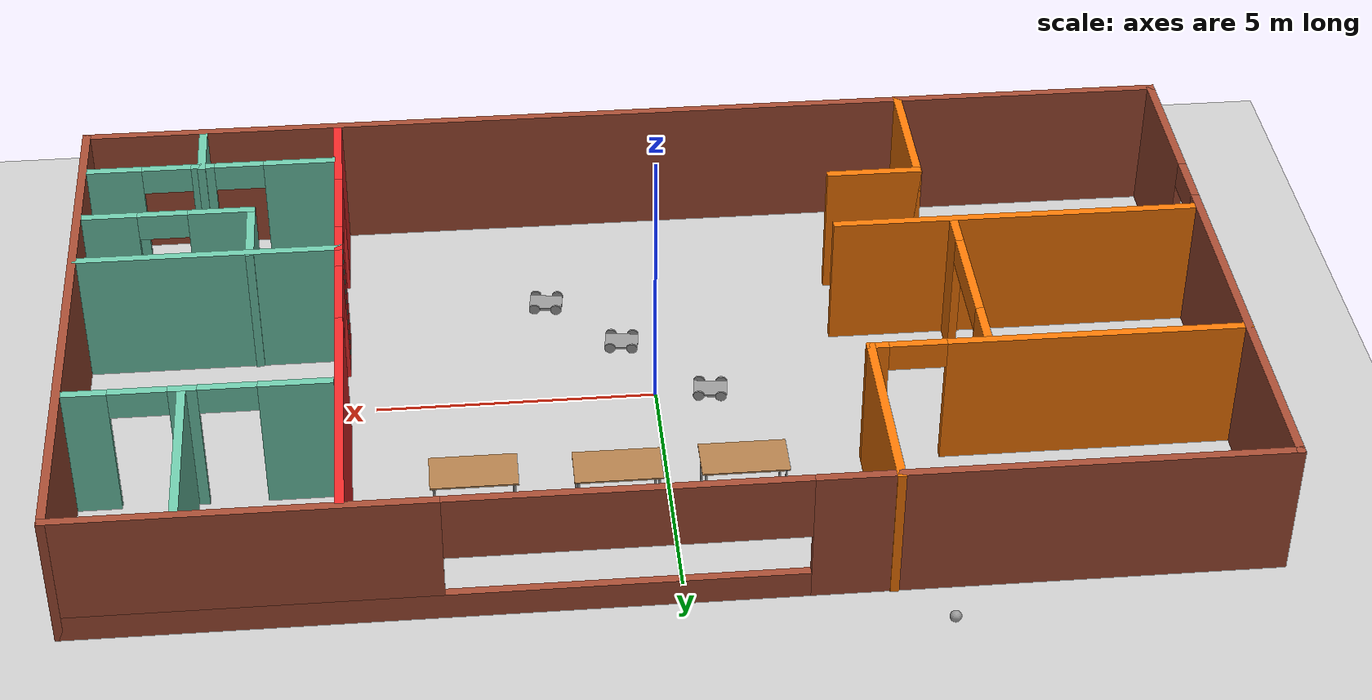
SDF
<sdf version="1.6">
 <world name="default">
  <plugin name="welcome" filename="libwelcome.so"/>
  <light name="sun" type="directional">
   <pose>0 0 10 0 -0 0</pose>
   <diffuse>0.8 0.8 0.8 1</diffuse>
   <specular>0.2 0.2 0.2 1</specular>
   <attenuation>
    <range>1000</range>
    <constant>0.9</constant>
    <linear>0.01</linear>
    <quadratic>0.001</quadratic>
   </attenuation>
   <direction>-0.5 0.1 -0.9</direction>
  </light>
  <model name="ground_plane">
   <static>1</static>
   <link name="link">
    <collision name="collision">
     <geometry><plane><normal>0 0 1</normal><size>100 100</size></plane></geometry>
     <surface>
      <contact><collide_bitmask>65535</collide_bitmask></contact>
      <friction><ode><mu>100</mu><mu2>50</mu2></ode></friction>
     </surface>
    </collision>
    <visual name="visual">
     <cast_shadows>0</cast_shadows>
     <geometry><plane><normal>0 0 1</normal><size>100 100</size></plane></geometry>
     <material>
      <script><uri>file://media/materials/scripts/gazebo.material</uri><name>Gazebo/Grey</name></script>
     </material>
    </visual>
   </link>
  </model>
  <gravity>0 0 -9.8</gravity>
  <magnetic_field>6e-06 2.3e-05 -4.2e-05</magnetic_field>
  <atmosphere type="adiabatic"/>
  <physics name="default_physics" default="0" type="ode">
   <max_step_size>0.001</max_step_size>
   <real_time_factor>1</real_time_factor>
   <real_time_update_rate>1000</real_time_update_rate>
  </physics>
  <scene><ambient>0.4 0.4 0.4 1</ambient><background>0.7 0.7 0.7 1</background><shadows>1</shadows></scene>
  <audio><device>default</device></audio>
  <spherical_coordinates>
   <surface_model>EARTH_WGS84</surface_model>
   <latitude_deg>0</latitude_deg>
   <longitude_deg>0</longitude_deg>
   <elevation>0</elevation>
   <heading_deg>0</heading_deg>
  </spherical_coordinates>
  <model name="building">
   <pose>0.099988 -0.03805 0 0 -0 0</pose>
   <link name="Wall_37">
    <collision name="Wall_37_Collision">
     <geometry><box><size>20.35 0.15 2.5</size></box></geometry>
     <pose>0 0 1.25 0 -0 0</pose>
    </collision>
    <visual name="Wall_37_Visual">
     <pose>0 0 1.25 0 -0 0</pose>
     <geometry><box><size>20.35 0.15 2.5</size></box></geometry>
     <material>
      <script><uri>file://media/materials/scripts/gazebo.material</uri><name>Gazebo/Bricks</name></script>
      <ambient>1 1 1 1</ambient>
     </material>
     <meta><layer>0</layer></meta>
    </visual>
    <pose>1.2e-05 -5.43545 0 0 -0 -0.002228</pose>
   </link>
   <link name="Wall_38">
    <collision name="Wall_38_Collision">
     <geometry><box><size>11.046 0.15 2.5</size></box></geometry>
     <pose>0 0 1.25 0 -0 0</pose>
    </collision>
    <visual name="Wall_38_Visual">
     <pose>0 0 1.25 0 -0 0</pose>
     <geometry><box><size>11.046 0.15 2.5</size></box></geometry>
     <material>
      <script><uri>file://media/materials/scripts/gazebo.material</uri><name>Gazebo/Bricks</name></script>
      <ambient>1 1 1 1</ambient>
     </material>
     <meta><layer>0</layer></meta>
    </visual>
    <pose>10.1 -0.009946 0 0 -0 1.5708</pose>
   </link>
   <link name="Wall_40">
    <pose>-10.1 0.012554 0 0 -0 1.5708</pose>
    <visual name="Wall_40_Visual_0">
     <pose>-4.15449 0 1.25 0 -0 0</pose>
     <geometry><box><size>2.69103 0.15 2.5</size></box></geometry>
     <material>
      <script><uri>file://media/materials/scripts/gazebo.material</uri><name>Gazebo/Bricks</name></script>
      <ambient>1 1 1 1</ambient>
     </material>
     <meta><layer>0</layer></meta>
    </visual>
    <collision name="Wall_40_Collision_0">
     <geometry><box><size>2.69103 0.15 2.5</size></box></geometry>
     <pose>-4.15449 0 1.25 0 -0 0</pose>
    </collision>
    <visual name="Wall_40_Visual_1">
     <pose>1.84551 0 1.25 0 -0 0</pose>
     <geometry><box><size>7.30897 0.15 2.5</size></box></geometry>
     <material>
      <script><uri>file://media/materials/scripts/gazebo.material</uri><name>Gazebo/Bricks</name></script>
      <ambient>1 1 1 1</ambient>
     </material>
     <meta><layer>0</layer></meta>
    </visual>
    <collision name="Wall_40_Collision_1">
     <geometry><box><size>7.30897 0.15 2.5</size></box></geometry>
     <pose>1.84551 0 1.25 0 -0 0</pose>
    </collision>
    <visual name="Wall_40_Visual_2">
     <pose>-2.30897 0 2.25 0 -0 0</pose>
     <geometry><box><size>1 0.15 0.5</size></box></geometry>
     <material>
      <script><uri>file://media/materials/scripts/gazebo.material</uri><name>Gazebo/Bricks</name></script>
      <ambient>1 1 1 1</ambient>
     </material>
     <meta><layer>0</layer></meta>
    </visual>
    <collision name="Wall_40_Collision_2">
     <geometry><box><size>1 0.15 0.5</size></box></geometry>
     <pose>-2.30897 0 2.25 0 -0 0</pose>
    </collision>
   </link>
   <link name="Wall_42">
    <collision name="Wall_42_Collision">
     <geometry><box><size>6.75 0.15 2.5</size></box></geometry>
     <pose>0 0 1.25 0 -0 0</pose>
    </collision>
    <visual name="Wall_42_Visual">
     <pose>0 0 1.25 0 -0 0</pose>
     <geometry><box><size>6.75 0.15 2.5</size></box></geometry>
     <material>
      <script><uri>file://media/materials/scripts/gazebo.material</uri><name>Gazebo/Grey</name></script>
      <ambient>0.996078 0.47451 0.0196078 1</ambient>
     </material>
     <meta><layer>0</layer></meta>
    </visual>
    <pose>-6.79999 -1.45995 0 0 -0 0</pose>
   </link>
   <link name="Wall_44">
    <pose>-6.83449 2.10805 0 0 -0 0</pose>
    <visual name="Wall_44_Visual_0">
     <pose>-0.692963 0 1.25 0 -0 0</pose>
     <geometry><box><size>5.29546 0.15 2.5</size></box></geometry>
     <material>
      <script><uri>file://media/materials/scripts/gazebo.material</uri><name>Gazebo/Grey</name></script>
      <ambient>0.996078 0.47451 0.0196078 1</ambient>
     </material>
     <meta><layer>0</layer></meta>
    </visual>
    <collision name="Wall_44_Collision_0">
     <geometry><box><size>5.29546 0.15 2.5</size></box></geometry>
     <pose>-0.692963 0 1.25 0 -0 0</pose>
    </collision>
    <visual name="Wall_44_Visual_1">
     <pose>3.14773 0 1.25 0 -0 0</pose>
     <geometry><box><size>0.385926 0.15 2.5</size></box></geometry>
     <material>
      <script><uri>file://media/materials/scripts/gazebo.material</uri><name>Gazebo/Grey</name></script>
      <ambient>0.996078 0.47451 0.0196078 1</ambient>
     </material>
     <meta><layer>0</layer></meta>
    </visual>
    <collision name="Wall_44_Collision_1">
     <geometry><box><size>0.385926 0.15 2.5</size></box></geometry>
     <pose>3.14773 0 1.25 0 -0 0</pose>
    </collision>
    <visual name="Wall_44_Visual_2">
     <pose>2.45477 0 2.25 0 -0 0</pose>
     <geometry><box><size>1 0.15 0.5</size></box></geometry>
     <material>
      <script><uri>file://media/materials/scripts/gazebo.material</uri><name>Gazebo/Grey</name></script>
      <ambient>0.996078 0.47451 0.0196078 1</ambient>
     </material>
     <meta><layer>0</layer></meta>
    </visual>
    <collision name="Wall_44_Collision_2">
     <geometry><box><size>1 0.15 0.5</size></box></geometry>
     <pose>2.45477 0 2.25 0 -0 0</pose>
    </collision>
   </link>
   <link name="Wall_45">
    <collision name="Wall_45_Collision">
     <geometry><box><size>3.5 0.15 2.5</size></box></geometry>
     <pose>0 0 1.25 0 -0 0</pose>
    </collision>
    <visual name="Wall_45_Visual">
     <pose>0 0 1.25 0 -0 0</pose>
     <geometry><box><size>3.5 0.15 2.5</size></box></geometry>
     <material>
      <script><uri>file://media/materials/scripts/gazebo.material</uri><name>Gazebo/Grey</name></script>
      <ambient>0.996078 0.47451 0.0196078 1</ambient>
     </material>
     <meta><layer>0</layer></meta>
    </visual>
    <pose>-3.5688 3.7831 0 0 -0 1.57068</pose>
   </link>
   <link name="Wall_47">
    <pose>5.41944 1.9014 0 0 -0 1.5708</pose>
    <visual name="Wall_47_Visual_0">
     <pose>-3.18321 0 1.25 0 -0 0</pose>
     <geometry><box><size>0.633579 0.15 2.5</size></box></geometry>
     <material>
      <script><uri>file://media/materials/scripts/gazebo.material</uri><name>Gazebo/Grey</name></script>
      <ambient>0.937255 0.160784 0.160784 1</ambient>
     </material>
     <meta><layer>0</layer></meta>
    </visual>
    <collision name="Wall_47_Collision_0">
     <geometry><box><size>0.633579 0.15 2.5</size></box></geometry>
     <pose>-3.18321 0 1.25 0 -0 0</pose>
    </collision>
    <visual name="Wall_47_Visual_1">
     <pose>1.06679 0 1.25 0 -0 0</pose>
     <geometry><box><size>4.86642 0.15 2.5</size></box></geometry>
     <material>
      <script><uri>file://media/materials/scripts/gazebo.material</uri><name>Gazebo/Grey</name></script>
      <ambient>0.937255 0.160784 0.160784 1</ambient>
     </material>
     <meta><layer>0</layer></meta>
    </visual>
    <collision name="Wall_47_Collision_1">
     <geometry><box><size>4.86642 0.15 2.5</size></box></geometry>
     <pose>1.06679 0 1.25 0 -0 0</pose>
    </collision>
    <visual name="Wall_47_Visual_2">
     <pose>-2.11642 0 2.25 0 -0 0</pose>
     <geometry><box><size>1.5 0.15 0.5</size></box></geometry>
     <material>
      <script><uri>file://media/materials/scripts/gazebo.material</uri><name>Gazebo/Grey</name></script>
      <ambient>0.937255 0.160784 0.160784 1</ambient>
     </material>
     <meta><layer>0</layer></meta>
    </visual>
    <collision name="Wall_47_Collision_2">
     <geometry><box><size>1.5 0.15 0.5</size></box></geometry>
     <pose>-2.11642 0 2.25 0 -0 0</pose>
    </collision>
   </link>
   <link name="Wall_49">
    <pose>1.2e-05 5.43805 0 0 -0 0</pose>
    <visual name="Wall_49_Visual_0">
     <pose>-6.17418 0 1.25 0 -0 0</pose>
     <geometry><box><size>8.00169 0.15 2.5</size></box></geometry>
     <material>
      <script><uri>file://media/materials/scripts/gazebo.material</uri><name>Gazebo/Bricks</name></script>
      <ambient>1 1 1 1</ambient>
     </material>
     <meta><layer>0</layer></meta>
    </visual>
    <collision name="Wall_49_Collision_0">
     <geometry><box><size>8.00169 0.15 2.5</size></box></geometry>
     <pose>-6.17418 0 1.25 0 -0 0</pose>
    </collision>
    <visual name="Wall_49_Visual_1">
     <pose>4.00084 0 0.25 0 -0 0</pose>
     <geometry><box><size>12.3484 0.15 0.5</size></box></geometry>
     <material>
      <script><uri>file://media/materials/scripts/gazebo.material</uri><name>Gazebo/Bricks</name></script>
      <ambient>1 1 1 1</ambient>
     </material>
     <meta><layer>0</layer></meta>
    </visual>
    <collision name="Wall_49_Collision_1">
     <geometry><box><size>12.3484 0.15 0.5</size></box></geometry>
     <pose>4.00084 0 0.25 0 -0 0</pose>
    </collision>
    <visual name="Wall_49_Visual_2">
     <pose>7.00084 0 1.5 0 -0 0</pose>
     <geometry><box><size>6.34836 0.15 2</size></box></geometry>
     <material>
      <script><uri>file://media/materials/scripts/gazebo.material</uri><name>Gazebo/Bricks</name></script>
      <ambient>1 1 1 1</ambient>
     </material>
     <meta><layer>0</layer></meta>
    </visual>
    <collision name="Wall_49_Collision_2">
     <geometry><box><size>6.34836 0.15 2</size></box></geometry>
     <pose>7.00084 0 1.5 0 -0 0</pose>
    </collision>
    <visual name="Wall_49_Visual_3">
     <pose>0.826666 0 1.9 0 -0 0</pose>
     <geometry><box><size>6 0.15 1.2</size></box></geometry>
     <material>
      <script><uri>file://media/materials/scripts/gazebo.material</uri><name>Gazebo/Bricks</name></script>
      <ambient>1 1 1 1</ambient>
     </material>
     <meta><layer>0</layer></meta>
    </visual>
    <collision name="Wall_49_Collision_3">
     <geometry><box><size>6 0.15 1.2</size></box></geometry>
     <pose>0.826666 0 1.9 0 -0 0</pose>
    </collision>
   </link>
   <link name="Wall_51">
    <pose>7.83851 2.24905 0 0 -0 0</pose>
    <visual name="Wall_51_Visual_0">
     <pose>-1.70105 0 1.25 0 -0 0</pose>
     <geometry><box><size>1.2709 0.15 2.5</size></box></geometry>
     <material>
      <script><uri>file://media/materials/scripts/gazebo.material</uri><name>Gazebo/Grey</name></script>
      <ambient>0.435294 0.796078 0.67451 1</ambient>
     </material>
     <meta><layer>0</layer></meta>
    </visual>
    <collision name="Wall_51_Collision_0">
     <geometry><box><size>1.2709 0.15 2.5</size></box></geometry>
     <pose>-1.70105 0 1.25 0 -0 0</pose>
    </collision>
    <visual name="Wall_51_Visual_1">
     <pose>0.179968 0 1.25 0 -0 0</pose>
     <geometry><box><size>0.491132 0.15 2.5</size></box></geometry>
     <material>
      <script><uri>file://media/materials/scripts/gazebo.material</uri><name>Gazebo/Grey</name></script>
      <ambient>0.435294 0.796078 0.67451 1</ambient>
     </material>
     <meta><layer>0</layer></meta>
    </visual>
    <collision name="Wall_51_Collision_1">
     <geometry><box><size>0.491132 0.15 2.5</size></box></geometry>
     <pose>0.179968 0 1.25 0 -0 0</pose>
    </collision>
    <visual name="Wall_51_Visual_2">
     <pose>1.88102 0 1.25 0 -0 0</pose>
     <geometry><box><size>0.910966 0.15 2.5</size></box></geometry>
     <material>
      <script><uri>file://media/materials/scripts/gazebo.material</uri><name>Gazebo/Grey</name></script>
      <ambient>0.435294 0.796078 0.67451 1</ambient>
     </material>
     <meta><layer>0</layer></meta>
    </visual>
    <collision name="Wall_51_Collision_2">
     <geometry><box><size>0.910966 0.15 2.5</size></box></geometry>
     <pose>1.88102 0 1.25 0 -0 0</pose>
    </collision>
    <visual name="Wall_51_Visual_3">
     <pose>-0.565598 0 2.25 0 -0 0</pose>
     <geometry><box><size>1 0.15 0.5</size></box></geometry>
     <material>
      <script><uri>file://media/materials/scripts/gazebo.material</uri><name>Gazebo/Grey</name></script>
      <ambient>0.435294 0.796078 0.67451 1</ambient>
     </material>
     <meta><layer>0</layer></meta>
    </visual>
    <collision name="Wall_51_Collision_3">
     <geometry><box><size>1 0.15 0.5</size></box></geometry>
     <pose>-0.565598 0 2.25 0 -0 0</pose>
    </collision>
    <visual name="Wall_51_Visual_4">
     <pose>0.925534 0 2.25 0 -0 0</pose>
     <geometry><box><size>1 0.15 0.5</size></box></geometry>
     <material>
      <script><uri>file://media/materials/scripts/gazebo.material</uri><name>Gazebo/Grey</name></script>
      <ambient>0.435294 0.796078 0.67451 1</ambient>
     </material>
     <meta><layer>0</layer></meta>
    </visual>
    <collision name="Wall_51_Collision_4">
     <geometry><box><size>1 0.15 0.5</size></box></geometry>
     <pose>0.925534 0 2.25 0 -0 0</pose>
    </collision>
   </link>
   <link name="Wall_53">
    <collision name="Wall_53_Collision">
     <geometry><box><size>3.28078 0.15 2.5</size></box></geometry>
     <pose>0 0 1.25 0 -0 0</pose>
    </collision>
    <visual name="Wall_53_Visual">
     <pose>0 0 1.25 0 -0 0</pose>
     <geometry><box><size>3.28078 0.15 2.5</size></box></geometry>
     <material>
      <script><uri>file://media/materials/scripts/gazebo.material</uri><name>Gazebo/Grey</name></script>
      <ambient>0.435294 0.796078 0.67451 1</ambient>
     </material>
     <meta><layer>0</layer></meta>
    </visual>
    <pose>8.03001 3.87255 0 0 -0 -1.5708</pose>
   </link>
   <link name="Wall_55">
    <collision name="Wall_55_Collision">
     <geometry><box><size>1.5 0.15 2.5</size></box></geometry>
     <pose>0 0 1.25 0 -0 0</pose>
    </collision>
    <visual name="Wall_55_Visual">
     <pose>0 0 1.25 0 -0 0</pose>
     <geometry><box><size>1.5 0.15 2.5</size></box></geometry>
     <material>
      <script><uri>file://media/materials/scripts/gazebo.material</uri><name>Gazebo/Grey</name></script>
      <ambient>0.435294 0.796078 0.67451 1</ambient>
     </material>
     <meta><layer>0</layer></meta>
    </visual>
    <pose>6.98497 -2.16679 0 0 -0 -1.5708</pose>
   </link>
   <link name="Wall_56">
    <pose>8.53497 -2.84179 0 0 -0 0</pose>
    <visual name="Wall_56_Visual_0">
     <pose>-1.01663 0 1.25 0 -0 0</pose>
     <geometry><box><size>1.21674 0.15 2.5</size></box></geometry>
     <material>
      <script><uri>file://media/materials/scripts/gazebo.material</uri><name>Gazebo/Grey</name></script>
      <ambient>0.435294 0.796078 0.67451 1</ambient>
     </material>
     <meta><layer>0</layer></meta>
    </visual>
    <collision name="Wall_56_Collision_0">
     <geometry><box><size>1.21674 0.15 2.5</size></box></geometry>
     <pose>-1.01663 0 1.25 0 -0 0</pose>
    </collision>
    <visual name="Wall_56_Visual_1">
     <pose>1.05837 0 1.25 0 -0 0</pose>
     <geometry><box><size>1.13326 0.15 2.5</size></box></geometry>
     <material>
      <script><uri>file://media/materials/scripts/gazebo.material</uri><name>Gazebo/Grey</name></script>
      <ambient>0.435294 0.796078 0.67451 1</ambient>
     </material>
     <meta><layer>0</layer></meta>
    </visual>
    <collision name="Wall_56_Collision_1">
     <geometry><box><size>1.13326 0.15 2.5</size></box></geometry>
     <pose>1.05837 0 1.25 0 -0 0</pose>
    </collision>
    <visual name="Wall_56_Visual_2">
     <pose>0.041741 0 2.25 0 -0 0</pose>
     <geometry><box><size>0.9 0.15 0.5</size></box></geometry>
     <material>
      <script><uri>file://media/materials/scripts/gazebo.material</uri><name>Gazebo/Grey</name></script>
      <ambient>0.435294 0.796078 0.67451 1</ambient>
     </material>
     <meta><layer>0</layer></meta>
    </visual>
    <collision name="Wall_56_Collision_2">
     <geometry><box><size>0.9 0.15 0.5</size></box></geometry>
     <pose>0.041741 0 2.25 0 -0 0</pose>
    </collision>
   </link>
   <link name="Wall_58">
    <pose>7.81601 -4.30195 0 0 -0 0</pose>
    <visual name="Wall_58_Visual_0">
     <pose>-1.68725 0 1.25 0 -0 0</pose>
     <geometry><box><size>1.3258 0.15 2.5</size></box></geometry>
     <material>
      <script><uri>file://media/materials/scripts/gazebo.material</uri><name>Gazebo/Grey</name></script>
      <ambient>0.435294 0.796078 0.67451 1</ambient>
     </material>
     <meta><layer>0</layer></meta>
    </visual>
    <collision name="Wall_58_Collision_0">
     <geometry><box><size>1.3258 0.15 2.5</size></box></geometry>
     <pose>-1.68725 0 1.25 0 -0 0</pose>
    </collision>
    <visual name="Wall_58_Visual_1">
     <pose>0.089658 0 1.25 0 -0 0</pose>
     <geometry><box><size>0.428016 0.15 2.5</size></box></geometry>
     <material>
      <script><uri>file://media/materials/scripts/gazebo.material</uri><name>Gazebo/Grey</name></script>
      <ambient>0.435294 0.796078 0.67451 1</ambient>
     </material>
     <meta><layer>0</layer></meta>
    </visual>
    <collision name="Wall_58_Collision_1">
     <geometry><box><size>0.428016 0.15 2.5</size></box></geometry>
     <pose>0.089658 0 1.25 0 -0 0</pose>
    </collision>
    <visual name="Wall_58_Visual_2">
     <pose>1.77691 0 1.25 0 -0 0</pose>
     <geometry><box><size>1.14649 0.15 2.5</size></box></geometry>
     <material>
      <script><uri>file://media/materials/scripts/gazebo.material</uri><name>Gazebo/Grey</name></script>
      <ambient>0.435294 0.796078 0.67451 1</ambient>
     </material>
     <meta><layer>0</layer></meta>
    </visual>
    <collision name="Wall_58_Collision_2">
     <geometry><box><size>1.14649 0.15 2.5</size></box></geometry>
     <pose>1.77691 0 1.25 0 -0 0</pose>
    </collision>
    <visual name="Wall_58_Visual_3">
     <pose>-0.57435 0 2.25 0 -0 0</pose>
     <geometry><box><size>0.9 0.15 0.5</size></box></geometry>
     <material>
      <script><uri>file://media/materials/scripts/gazebo.material</uri><name>Gazebo/Grey</name></script>
      <ambient>0.435294 0.796078 0.67451 1</ambient>
     </material>
     <meta><layer>0</layer></meta>
    </visual>
    <collision name="Wall_58_Collision_3">
     <geometry><box><size>0.9 0.15 0.5</size></box></geometry>
     <pose>-0.57435 0 2.25 0 -0 0</pose>
    </collision>
    <visual name="Wall_58_Visual_4">
     <pose>0.753665 0 2.25 0 -0 0</pose>
     <geometry><box><size>0.9 0.15 0.5</size></box></geometry>
     <material>
      <script><uri>file://media/materials/scripts/gazebo.material</uri><name>Gazebo/Grey</name></script>
      <ambient>0.435294 0.796078 0.67451 1</ambient>
     </material>
     <meta><layer>0</layer></meta>
    </visual>
    <collision name="Wall_58_Collision_4">
     <geometry><box><size>0.9 0.15 0.5</size></box></geometry>
     <pose>0.753665 0 2.25 0 -0 0</pose>
    </collision>
   </link>
   <link name="Wall_62">
    <pose>5.41944 -3.4486 0 0 -0 -1.5708</pose>
    <visual name="Wall_62_Visual_0">
     <pose>-1.64393 0 1.25 0 -0 0</pose>
     <geometry><box><size>0.71215 0.15 2.5</size></box></geometry>
     <material>
      <script><uri>file://media/materials/scripts/gazebo.material</uri><name>Gazebo/Grey</name></script>
      <ambient>0.937255 0.160784 0.160784 1</ambient>
     </material>
     <meta><layer>0</layer></meta>
    </visual>
    <collision name="Wall_62_Collision_0">
     <geometry><box><size>0.71215 0.15 2.5</size></box></geometry>
     <pose>-1.64393 0 1.25 0 -0 0</pose>
    </collision>
    <visual name="Wall_62_Visual_1">
     <pose>1.10607 0 1.25 0 -0 0</pose>
     <geometry><box><size>1.78785 0.15 2.5</size></box></geometry>
     <material>
      <script><uri>file://media/materials/scripts/gazebo.material</uri><name>Gazebo/Grey</name></script>
      <ambient>0.937255 0.160784 0.160784 1</ambient>
     </material>
     <meta><layer>0</layer></meta>
    </visual>
    <collision name="Wall_62_Collision_1">
     <geometry><box><size>1.78785 0.15 2.5</size></box></geometry>
     <pose>1.10607 0 1.25 0 -0 0</pose>
    </collision>
    <visual name="Wall_62_Visual_2">
     <pose>-0.53785 0 2.25 0 -0 0</pose>
     <geometry><box><size>1.5 0.15 0.5</size></box></geometry>
     <material>
      <script><uri>file://media/materials/scripts/gazebo.material</uri><name>Gazebo/Grey</name></script>
      <ambient>0.937255 0.160784 0.160784 1</ambient>
     </material>
     <meta><layer>0</layer></meta>
    </visual>
    <collision name="Wall_62_Collision_2">
     <geometry><box><size>1.5 0.15 0.5</size></box></geometry>
     <pose>-0.53785 0 2.25 0 -0 0</pose>
    </collision>
   </link>
   <link name="Wall_64">
    <collision name="Wall_64_Collision">
     <geometry><box><size>2.5 0.15 2.5</size></box></geometry>
     <pose>0 0 1.25 0 -0 0</pose>
    </collision>
    <visual name="Wall_64_Visual">
     <pose>0 0 1.25 0 -0 0</pose>
     <geometry><box><size>2.5 0.15 2.5</size></box></geometry>
     <material>
      <script><uri>file://media/materials/scripts/gazebo.material</uri><name>Gazebo/Grey</name></script>
      <ambient>0.996078 0.47451 0.0196078 1</ambient>
     </material>
     <meta><layer>0</layer></meta>
    </visual>
    <pose>-5.20386 -4.21882 0 0 -0 1.5708</pose>
   </link>
   <link name="Wall_65">
    <collision name="Wall_65_Collision">
     <geometry><box><size>1.75 0.15 2.5</size></box></geometry>
     <pose>0 0 1.25 0 -0 0</pose>
    </collision>
    <visual name="Wall_65_Visual">
     <pose>0 0 1.25 0 -0 0</pose>
     <geometry><box><size>1.75 0.15 2.5</size></box></geometry>
     <material>
      <script><uri>file://media/materials/scripts/gazebo.material</uri><name>Gazebo/Grey</name></script>
      <ambient>0.996078 0.47451 0.0196078 1</ambient>
     </material>
     <meta><layer>0</layer></meta>
    </visual>
    <pose>-4.40386 -3.04382 0 0 -0 0</pose>
   </link>
   <link name="Wall_67">
    <pose>-5.59388 0.356914 0 0 -0 -1.5708</pose>
    <visual name="Wall_67_Visual_0">
     <pose>-1.30933 0 1.25 0 -0 0</pose>
     <geometry><box><size>0.881338 0.15 2.5</size></box></geometry>
     <material>
      <script><uri>file://media/materials/scripts/gazebo.material</uri><name>Gazebo/Grey</name></script>
      <ambient>0.996078 0.47451 0.0196078 1</ambient>
     </material>
     <meta><layer>0</layer></meta>
    </visual>
    <collision name="Wall_67_Collision_0">
     <geometry><box><size>0.881338 0.15 2.5</size></box></geometry>
     <pose>-1.30933 0 1.25 0 -0 0</pose>
    </collision>
    <visual name="Wall_67_Visual_1">
     <pose>1.44067 0 1.25 0 -0 0</pose>
     <geometry><box><size>0.618662 0.15 2.5</size></box></geometry>
     <material>
      <script><uri>file://media/materials/scripts/gazebo.material</uri><name>Gazebo/Grey</name></script>
      <ambient>0.996078 0.47451 0.0196078 1</ambient>
     </material>
     <meta><layer>0</layer></meta>
    </visual>
    <collision name="Wall_67_Collision_1">
     <geometry><box><size>0.618662 0.15 2.5</size></box></geometry>
     <pose>1.44067 0 1.25 0 -0 0</pose>
    </collision>
    <visual name="Wall_67_Visual_2">
     <pose>0.131338 0 2.25 0 -0 0</pose>
     <geometry><box><size>2 0.15 0.5</size></box></geometry>
     <material>
      <script><uri>file://media/materials/scripts/gazebo.material</uri><name>Gazebo/Grey</name></script>
      <ambient>0.996078 0.47451 0.0196078 1</ambient>
     </material>
     <meta><layer>0</layer></meta>
    </visual>
    <collision name="Wall_67_Collision_2">
     <geometry><box><size>2 0.15 0.5</size></box></geometry>
     <pose>0.131338 0 2.25 0 -0 0</pose>
    </collision>
   </link>
   <link name="Wall_69">
    <collision name="Wall_69_Collision">
     <geometry><box><size>1.25 0.15 2.5</size></box></geometry>
     <pose>0 0 1.25 0 -0 0</pose>
    </collision>
    <visual name="Wall_69_Visual">
     <pose>0 0 1.25 0 -0 0</pose>
     <geometry><box><size>1.25 0.15 2.5</size></box></geometry>
     <material>
      <script><uri>file://media/materials/scripts/gazebo.material</uri><name>Gazebo/Grey</name></script>
      <ambient>0.435294 0.796078 0.67451 1</ambient>
     </material>
     <meta><layer>0</layer></meta>
    </visual>
    <pose>7.92773 -4.82494 0 0 -0 -1.5708</pose>
   </link>
   <link name="Wall_73">
    <collision name="Wall_73_Collision">
     <geometry><box><size>4.75 0.15 2.5</size></box></geometry>
     <pose>0 0 1.25 0 -0 0</pose>
    </collision>
    <visual name="Wall_73_Visual">
     <pose>0 0 1.25 0 -0 0</pose>
     <geometry><box><size>4.75 0.15 2.5</size></box></geometry>
     <material>
      <script><uri>file://media/materials/scripts/gazebo.material</uri><name>Gazebo/Grey</name></script>
      <ambient>0.435294 0.796078 0.67451 1</ambient>
     </material>
     <meta><layer>0</layer></meta>
    </visual>
    <pose>7.71944 -1.5236 0 0 -0 0</pose>
   </link>
   <static>1</static>
  </model>
  <model name="table">
   <static>1</static>
   <link name="link">
    <collision name="surface">
     <pose>0 0 1 0 -0 0</pose>
     <geometry><box><size>1.5 0.8 0.03</size></box></geometry>
     <surface><friction><ode><mu>0.6</mu><mu2>0.6</mu2></ode></friction></surface>
    </collision>
    <visual name="visual1">
     <pose>0 0 1 0 -0 0</pose>
     <geometry><box><size>1.5 0.8 0.03</size></box></geometry>
     <material>
      <script><uri>file://media/materials/scripts/gazebo.material</uri><name>Gazebo/Wood</name></script>
     </material>
    </visual>
    <collision name="front_left_leg">
     <pose>0.68 0.38 0.5 0 -0 0</pose>
     <geometry><cylinder><radius>0.02</radius><length>1</length></cylinder></geometry>
    </collision>
    <visual name="front_left_leg">
     <pose>0.68 0.38 0.5 0 -0 0</pose>
     <geometry><cylinder><radius>0.02</radius><length>1</length></cylinder></geometry>
     <material>
      <script><uri>file://media/materials/scripts/gazebo.material</uri><name>Gazebo/Grey</name></script>
     </material>
    </visual>
    <collision name="front_right_leg">
     <pose>0.68 -0.38 0.5 0 -0 0</pose>
     <geometry><cylinder><radius>0.02</radius><length>1</length></cylinder></geometry>
    </collision>
    <visual name="front_right_leg">
     <pose>0.68 -0.38 0.5 0 -0 0</pose>
     <geometry><cylinder><radius>0.02</radius><length>1</length></cylinder></geometry>
     <material>
      <script><uri>file://media/materials/scripts/gazebo.material</uri><name>Gazebo/Grey</name></script>
     </material>
    </visual>
    <collision name="back_right_leg">
     <pose>-0.68 -0.38 0.5 0 -0 0</pose>
     <geometry><cylinder><radius>0.02</radius><length>1</length></cylinder></geometry>
    </collision>
    <visual name="back_right_leg">
     <pose>-0.68 -0.38 0.5 0 -0 0</pose>
     <geometry><cylinder><radius>0.02</radius><length>1</length></cylinder></geometry>
     <material>
      <script><uri>file://media/materials/scripts/gazebo.material</uri><name>Gazebo/Grey</name></script>
     </material>
    </visual>
    <collision name="back_left_leg">
     <pose>-0.68 0.38 0.5 0 -0 0</pose>
     <geometry><cylinder><radius>0.02</radius><length>1</length></cylinder></geometry>
    </collision>
    <visual name="back_left_leg">
     <pose>-0.68 0.38 0.5 0 -0 0</pose>
     <geometry><cylinder><radius>0.02</radius><length>1</length></cylinder></geometry>
     <material>
      <script><uri>file://media/materials/scripts/gazebo.material</uri><name>Gazebo/Grey</name></script>
     </material>
    </visual>
   </link>
   <pose>-1.22708 3.03842 0 0 -0 0</pose>
  </model>
  <model name="table_clone">
   <static>1</static>
   <link name="link">
    <collision name="surface">
     <pose>0 0 1 0 -0 0</pose>
     <geometry><box><size>1.5 0.8 0.03</size></box></geometry>
     <surface><friction><ode><mu>0.6</mu><mu2>0.6</mu2></ode></friction></surface>
    </collision>
    <visual name="visual1">
     <pose>0 0 1 0 -0 0</pose>
     <geometry><box><size>1.5 0.8 0.03</size></box></geometry>
     <material>
      <script><uri>file://media/materials/scripts/gazebo.material</uri><name>Gazebo/Wood</name></script>
     </material>
    </visual>
    <collision name="front_left_leg">
     <pose>0.68 0.38 0.5 0 -0 0</pose>
     <geometry><cylinder><radius>0.02</radius><length>1</length></cylinder></geometry>
    </collision>
    <visual name="front_left_leg">
     <pose>0.68 0.38 0.5 0 -0 0</pose>
     <geometry><cylinder><radius>0.02</radius><length>1</length></cylinder></geometry>
     <material>
      <script><uri>file://media/materials/scripts/gazebo.material</uri><name>Gazebo/Grey</name></script>
     </material>
    </visual>
    <collision name="front_right_leg">
     <pose>0.68 -0.38 0.5 0 -0 0</pose>
     <geometry><cylinder><radius>0.02</radius><length>1</length></cylinder></geometry>
    </collision>
    <visual name="front_right_leg">
     <pose>0.68 -0.38 0.5 0 -0 0</pose>
     <geometry><cylinder><radius>0.02</radius><length>1</length></cylinder></geometry>
     <material>
      <script><uri>file://media/materials/scripts/gazebo.material</uri><name>Gazebo/Grey</name></script>
     </material>
    </visual>
    <collision name="back_right_leg">
     <pose>-0.68 -0.38 0.5 0 -0 0</pose>
     <geometry><cylinder><radius>0.02</radius><length>1</length></cylinder></geometry>
    </collision>
    <visual name="back_right_leg">
     <pose>-0.68 -0.38 0.5 0 -0 0</pose>
     <geometry><cylinder><radius>0.02</radius><length>1</length></cylinder></geometry>
     <material>
      <script><uri>file://media/materials/scripts/gazebo.material</uri><name>Gazebo/Grey</name></script>
     </material>
    </visual>
    <collision name="back_left_leg">
     <pose>-0.68 0.38 0.5 0 -0 0</pose>
     <geometry><cylinder><radius>0.02</radius><length>1</length></cylinder></geometry>
    </collision>
    <visual name="back_left_leg">
     <pose>-0.68 0.38 0.5 0 -0 0</pose>
     <geometry><cylinder><radius>0.02</radius><length>1</length></cylinder></geometry>
     <material>
      <script><uri>file://media/materials/scripts/gazebo.material</uri><name>Gazebo/Grey</name></script>
     </material>
    </visual>
   </link>
   <pose>0.927516 3.06631 0 0 -0 0</pose>
  </model>
  <model name="table_clone_0">
   <static>1</static>
   <link name="link">
    <collision name="surface">
     <pose>0 0 1 0 -0 0</pose>
     <geometry><box><size>1.5 0.8 0.03</size></box></geometry>
     <surface><friction><ode><mu>0.6</mu><mu2>0.6</mu2></ode></friction></surface>
    </collision>
    <visual name="visual1">
     <pose>0 0 1 0 -0 0</pose>
     <geometry><box><size>1.5 0.8 0.03</size></box></geometry>
     <material>
      <script><uri>file://media/materials/scripts/gazebo.material</uri><name>Gazebo/Wood</name></script>
     </material>
    </visual>
    <collision name="front_left_leg">
     <pose>0.68 0.38 0.5 0 -0 0</pose>
     <geometry><cylinder><radius>0.02</radius><length>1</length></cylinder></geometry>
    </collision>
    <visual name="front_left_leg">
     <pose>0.68 0.38 0.5 0 -0 0</pose>
     <geometry><cylinder><radius>0.02</radius><length>1</length></cylinder></geometry>
     <material>
      <script><uri>file://media/materials/scripts/gazebo.material</uri><name>Gazebo/Grey</name></script>
     </material>
    </visual>
    <collision name="front_right_leg">
     <pose>0.68 -0.38 0.5 0 -0 0</pose>
     <geometry><cylinder><radius>0.02</radius><length>1</length></cylinder></geometry>
    </collision>
    <visual name="front_right_leg">
     <pose>0.68 -0.38 0.5 0 -0 0</pose>
     <geometry><cylinder><radius>0.02</radius><length>1</length></cylinder></geometry>
     <material>
      <script><uri>file://media/materials/scripts/gazebo.material</uri><name>Gazebo/Grey</name></script>
     </material>
    </visual>
    <collision name="back_right_leg">
     <pose>-0.68 -0.38 0.5 0 -0 0</pose>
     <geometry><cylinder><radius>0.02</radius><length>1</length></cylinder></geometry>
    </collision>
    <visual name="back_right_leg">
     <pose>-0.68 -0.38 0.5 0 -0 0</pose>
     <geometry><cylinder><radius>0.02</radius><length>1</length></cylinder></geometry>
     <material>
      <script><uri>file://media/materials/scripts/gazebo.material</uri><name>Gazebo/Grey</name></script>
     </material>
    </visual>
    <collision name="back_left_leg">
     <pose>-0.68 0.38 0.5 0 -0 0</pose>
     <geometry><cylinder><radius>0.02</radius><length>1</length></cylinder></geometry>
    </collision>
    <visual name="back_left_leg">
     <pose>-0.68 0.38 0.5 0 -0 0</pose>
     <geometry><cylinder><radius>0.02</radius><length>1</length></cylinder></geometry>
     <material>
      <script><uri>file://media/materials/scripts/gazebo.material</uri><name>Gazebo/Grey</name></script>
     </material>
    </visual>
   </link>
   <pose>3.35676 3.00791 0 0 -0 0</pose>
  </model>
  <model name="bookshelf">
   <static>1</static>
   <link name="link">
    <inertial><mass>1</mass></inertial>
    <collision name="back">
     <pose>0 0.005 0.6 0 -0 0</pose>
     <geometry><box><size>0.9 0.01 1.2</size></box></geometry>
    </collision>
    <visual name="visual1">
     <pose>0 0.005 0.6 0 -0 0</pose>
     <geometry><box><size>0.9 0.01 1.2</size></box></geometry>
     <material>
      <script><uri>file://media/materials/scripts/gazebo.material</uri><name>Gazebo/Wood</name></script>
     </material>
    </visual>
    <collision name="left_side">
     <pose>0.45 -0.195 0.6 0 -0 0</pose>
     <geometry><box><size>0.02 0.4 1.2</size></box></geometry>
    </collision>
    <visual name="visual2">
     <pose>0.45 -0.195 0.6 0 -0 0</pose>
     <geometry><box><size>0.02 0.4 1.2</size></box></geometry>
     <material>
      <script><uri>file://media/materials/scripts/gazebo.material</uri><name>Gazebo/Wood</name></script>
     </material>
    </visual>
    <collision name="right_side">
     <pose>-0.45 -0.195 0.6 0 -0 0</pose>
     <geometry><box><size>0.02 0.4 1.2</size></box></geometry>
    </collision>
    <visual name="visual3">
     <pose>-0.45 -0.195 0.6 0 -0 0</pose>
     <geometry><box><size>0.02 0.4 1.2</size></box></geometry>
     <material>
      <script><uri>file://media/materials/scripts/gazebo.material</uri><name>Gazebo/Wood</name></script>
     </material>
    </visual>
    <collision name="bottom">
     <pose>0 -0.195 0.03 0 -0 0</pose>
     <geometry><box><size>0.88 0.4 0.06</size></box></geometry>
    </collision>
    <visual name="visual4">
     <pose>0 -0.195 0.03 0 -0 0</pose>
     <geometry><box><size>0.88 0.4 0.06</size></box></geometry>
     <material>
      <script><uri>file://media/materials/scripts/gazebo.material</uri><name>Gazebo/Wood</name></script>
     </material>
    </visual>
    <collision name="top">
     <pose>0 -0.195 1.19 0 -0 0</pose>
     <geometry><box><size>0.88 0.4 0.02</size></box></geometry>
    </collision>
    <visual name="visual5">
     <pose>0 -0.195 1.19 0 -0 0</pose>
     <geometry><box><size>0.88 0.4 0.02</size></box></geometry>
     <material>
      <script><uri>file://media/materials/scripts/gazebo.material</uri><name>Gazebo/Wood</name></script>
     </material>
    </visual>
    <collision name="low_shelf">
     <pose>0 -0.195 0.43 0 -0 0</pose>
     <geometry><box><size>0.88 0.4 0.02</size></box></geometry>
    </collision>
    <visual name="visual6">
     <pose>0 -0.195 0.43 0 -0 0</pose>
     <geometry><box><size>0.88 0.4 0.02</size></box></geometry>
     <material>
      <script><uri>file://media/materials/scripts/gazebo.material</uri><name>Gazebo/Wood</name></script>
     </material>
    </visual>
    <collision name="high_shelf">
     <pose>0 -0.195 0.8 0 -0 0</pose>
     <geometry><box><size>0.88 0.4 0.02</size></box></geometry>
    </collision>
    <visual name="visual7">
     <pose>0 -0.195 0.8 0 -0 0</pose>
     <geometry><box><size>0.88 0.4 0.02</size></box></geometry>
     <material>
      <script><uri>file://media/materials/scripts/gazebo.material</uri><name>Gazebo/Wood</name></script>
     </material>
    </visual>
   </link>
   <pose>7.55639 5.27585 0 0 -0 0</pose>
  </model>
  <model name="bookshelf_clone">
   <static>1</static>
   <link name="link">
    <inertial><mass>1</mass></inertial>
    <collision name="back">
     <pose>0 0.005 0.6 0 -0 0</pose>
     <geometry><box><size>0.9 0.01 1.2</size></box></geometry>
    </collision>
    <visual name="visual1">
     <pose>0 0.005 0.6 0 -0 0</pose>
     <geometry><box><size>0.9 0.01 1.2</size></box></geometry>
     <material>
      <script><uri>file://media/materials/scripts/gazebo.material</uri><name>Gazebo/Wood</name></script>
     </material>
    </visual>
    <collision name="left_side">
     <pose>0.45 -0.195 0.6 0 -0 0</pose>
     <geometry><box><size>0.02 0.4 1.2</size></box></geometry>
    </collision>
    <visual name="visual2">
     <pose>0.45 -0.195 0.6 0 -0 0</pose>
     <geometry><box><size>0.02 0.4 1.2</size></box></geometry>
     <material>
      <script><uri>file://media/materials/scripts/gazebo.material</uri><name>Gazebo/Wood</name></script>
     </material>
    </visual>
    <collision name="right_side">
     <pose>-0.45 -0.195 0.6 0 -0 0</pose>
     <geometry><box><size>0.02 0.4 1.2</size></box></geometry>
    </collision>
    <visual name="visual3">
     <pose>-0.45 -0.195 0.6 0 -0 0</pose>
     <geometry><box><size>0.02 0.4 1.2</size></box></geometry>
     <material>
      <script><uri>file://media/materials/scripts/gazebo.material</uri><name>Gazebo/Wood</name></script>
     </material>
    </visual>
    <collision name="bottom">
     <pose>0 -0.195 0.03 0 -0 0</pose>
     <geometry><box><size>0.88 0.4 0.06</size></box></geometry>
    </collision>
    <visual name="visual4">
     <pose>0 -0.195 0.03 0 -0 0</pose>
     <geometry><box><size>0.88 0.4 0.06</size></box></geometry>
     <material>
      <script><uri>file://media/materials/scripts/gazebo.material</uri><name>Gazebo/Wood</name></script>
     </material>
    </visual>
    <collision name="top">
     <pose>0 -0.195 1.19 0 -0 0</pose>
     <geometry><box><size>0.88 0.4 0.02</size></box></geometry>
    </collision>
    <visual name="visual5">
     <pose>0 -0.195 1.19 0 -0 0</pose>
     <geometry><box><size>0.88 0.4 0.02</size></box></geometry>
     <material>
      <script><uri>file://media/materials/scripts/gazebo.material</uri><name>Gazebo/Wood</name></script>
     </material>
    </visual>
    <collision name="low_shelf">
     <pose>0 -0.195 0.43 0 -0 0</pose>
     <geometry><box><size>0.88 0.4 0.02</size></box></geometry>
    </collision>
    <visual name="visual6">
     <pose>0 -0.195 0.43 0 -0 0</pose>
     <geometry><box><size>0.88 0.4 0.02</size></box></geometry>
     <material>
      <script><uri>file://media/materials/scripts/gazebo.material</uri><name>Gazebo/Wood</name></script>
     </material>
    </visual>
    <collision name="high_shelf">
     <pose>0 -0.195 0.8 0 -0 0</pose>
     <geometry><box><size>0.88 0.4 0.02</size></box></geometry>
    </collision>
    <visual name="visual7">
     <pose>0 -0.195 0.8 0 -0 0</pose>
     <geometry><box><size>0.88 0.4 0.02</size></box></geometry>
     <material>
      <script><uri>file://media/materials/scripts/gazebo.material</uri><name>Gazebo/Wood</name></script>
     </material>
    </visual>
   </link>
   <pose>9.62884 5.25887 0 0 -0 0</pose>
  </model>
  <model name="myRobot">
   <link name="link_0">
    <inertial>
     <mass>1</mass>
     <inertia>
      <ixx>0.166667</ixx>
      <ixy>0</ixy>
      <ixz>0</ixz>
      <iyy>0.166667</iyy>
      <iyz>0</iyz>
      <izz>0.166667</izz>
     </inertia>
     <pose>0 0 0.1 0 -0 0</pose>
    </inertial>
    <pose>0 0.009302 0 0 -0 0</pose>
    <visual name="visual">
     <geometry><box><size>0.6 0.4 0.05</size></box></geometry>
     <material>
      <lighting>1</lighting>
      <script><uri>file://media/materials/scripts/gazebo.material</uri><name>Gazebo/Grey</name></script>
      <shader type="vertex"><normal_map>__default__</normal_map></shader>
      <ambient>0.3 0.3 0.3 1</ambient>
      <diffuse>0.7 0.7 0.7 1</diffuse>
      <specular>0.01 0.01 0.01 1</specular>
      <emissive>0 0 0 1</emissive>
     </material>
    </visual>
    <collision name="collision">
     <geometry><box><size>0.6 0.4 0.05</size></box></geometry>
     <surface>
      <friction>
       <ode><mu>1</mu><mu2>1</mu2><fdir1>0 0 0</fdir1><slip1>0</slip1><slip2>0</slip2></ode>
       <torsional>
        <coefficient>1</coefficient>
        <patch_radius>0</patch_radius>
        <surface_radius>0</surface_radius>
        <use_patch_radius>1</use_patch_radius>
        <ode><slip>0</slip></ode>
       </torsional>
      </friction>
      <bounce><restitution_coefficient>0</restitution_coefficient><threshold>1e+06</threshold></bounce>
      <contact>
       <collide_without_contact>0</collide_without_contact>
       <collide_without_contact_bitmask>1</collide_without_contact_bitmask>
       <collide_bitmask>1</collide_bitmask>
       <ode>
        <soft_cfm>0</soft_cfm>
        <soft_erp>0.2</soft_erp>
        <kp>1e+13</kp>
        <kd>1</kd>
        <max_vel>0.01</max_vel>
        <min_depth>0</min_depth>
       </ode>
       <bullet>
        <split_impulse>1</split_impulse>
        <split_impulse_penetration_threshold>-0.01</split_impulse_penetration_threshold>
        <soft_cfm>0</soft_cfm>
        <soft_erp>0.2</soft_erp>
        <kp>1e+13</kp>
        <kd>1</kd>
       </bullet>
      </contact>
     </surface>
    </collision>
   </link>
   <link name="link_1">
    <inertial>
     <mass>1</mass>
     <inertia><ixx>0.145833</ixx><ixy>0</ixy><ixz>0</ixz><iyy>0.145833</iyy><iyz>0</iyz><izz>0.125</izz></inertia>
    </inertial>
    <pose>-0.2 0.212674 0 1.5707 -0 0</pose>
    <visual name="visual">
     <geometry><cylinder><radius>0.1</radius><length>0.03</length></cylinder></geometry>
     <material>
      <lighting>1</lighting>
      <script><uri>file://media/materials/scripts/gazebo.material</uri><name>Gazebo/Grey</name></script>
      <shader type="vertex"><normal_map>__default__</normal_map></shader>
      <ambient>0.3 0.3 0.3 1</ambient>
      <diffuse>0.7 0.7 0.7 1</diffuse>
      <specular>0.01 0.01 0.01 1</specular>
      <emissive>0 0 0 1</emissive>
     </material>
    </visual>
    <collision name="collision">
     <geometry><cylinder><radius>0.1</radius><length>0.03</length></cylinder></geometry>
     <surface>
      <friction>
       <ode><mu>1</mu><mu2>1</mu2><fdir1>0 0 0</fdir1><slip1>0</slip1><slip2>0</slip2></ode>
       <torsional>
        <coefficient>1</coefficient>
        <patch_radius>0</patch_radius>
        <surface_radius>0</surface_radius>
        <use_patch_radius>1</use_patch_radius>
        <ode><slip>0</slip></ode>
       </torsional>
      </friction>
      <bounce><restitution_coefficient>0</restitution_coefficient><threshold>1e+06</threshold></bounce>
      <contact>
       <collide_without_contact>0</collide_without_contact>
       <collide_without_contact_bitmask>1</collide_without_contact_bitmask>
       <collide_bitmask>1</collide_bitmask>
       <ode>
        <soft_cfm>0</soft_cfm>
        <soft_erp>0.2</soft_erp>
        <kp>1e+13</kp>
        <kd>1</kd>
        <max_vel>0.01</max_vel>
        <min_depth>0</min_depth>
       </ode>
       <bullet>
        <split_impulse>1</split_impulse>
        <split_impulse_penetration_threshold>-0.01</split_impulse_penetration_threshold>
        <soft_cfm>0</soft_cfm>
        <soft_erp>0.2</soft_erp>
        <kp>1e+13</kp>
        <kd>1</kd>
       </bullet>
      </contact>
     </surface>
    </collision>
   </link>
   <link name="link_1_clone">
    <inertial>
     <mass>1</mass>
     <inertia><ixx>0.145833</ixx><ixy>0</ixy><ixz>0</ixz><iyy>0.145833</iyy><iyz>0</iyz><izz>0.125</izz></inertia>
    </inertial>
    <pose>-0.2 -0.217336 0 1.5707 -0 0</pose>
    <visual name="visual">
     <geometry><cylinder><radius>0.1</radius><length>0.03</length></cylinder></geometry>
     <material>
      <lighting>1</lighting>
      <script><uri>file://media/materials/scripts/gazebo.material</uri><name>Gazebo/Grey</name></script>
      <shader type="vertex"><normal_map>__default__</normal_map></shader>
      <ambient>0.3 0.3 0.3 1</ambient>
      <diffuse>0.7 0.7 0.7 1</diffuse>
      <specular>0.01 0.01 0.01 1</specular>
      <emissive>0 0 0 1</emissive>
     </material>
    </visual>
    <collision name="collision">
     <geometry><cylinder><radius>0.1</radius><length>0.03</length></cylinder></geometry>
     <surface>
      <friction>
       <ode><mu>1</mu><mu2>1</mu2><fdir1>0 0 0</fdir1><slip1>0</slip1><slip2>0</slip2></ode>
       <torsional>
        <coefficient>1</coefficient>
        <patch_radius>0</patch_radius>
        <surface_radius>0</surface_radius>
        <use_patch_radius>1</use_patch_radius>
        <ode><slip>0</slip></ode>
       </torsional>
      </friction>
      <bounce><restitution_coefficient>0</restitution_coefficient><threshold>1e+06</threshold></bounce>
      <contact>
       <collide_without_contact>0</collide_without_contact>
       <collide_without_contact_bitmask>1</collide_without_contact_bitmask>
       <collide_bitmask>1</collide_bitmask>
       <ode>
        <soft_cfm>0</soft_cfm>
        <soft_erp>0.2</soft_erp>
        <kp>1e+13</kp>
        <kd>1</kd>
        <max_vel>0.01</max_vel>
        <min_depth>0</min_depth>
       </ode>
       <bullet>
        <split_impulse>1</split_impulse>
        <split_impulse_penetration_threshold>-0.01</split_impulse_penetration_threshold>
        <soft_cfm>0</soft_cfm>
        <soft_erp>0.2</soft_erp>
        <kp>1e+13</kp>
        <kd>1</kd>
       </bullet>
      </contact>
     </surface>
    </collision>
   </link>
   <link name="link_1_clone_0">
    <inertial>
     <mass>1</mass>
     <inertia><ixx>0.145833</ixx><ixy>0</ixy><ixz>0</ixz><iyy>0.145833</iyy><iyz>0</iyz><izz>0.125</izz></inertia>
    </inertial>
    <pose>0.2 -0.217326 0 1.5707 -0 0</pose>
    <visual name="visual">
     <geometry><cylinder><radius>0.1</radius><length>0.03</length></cylinder></geometry>
     <material>
      <lighting>1</lighting>
      <script><uri>file://media/materials/scripts/gazebo.material</uri><name>Gazebo/Grey</name></script>
      <shader type="vertex"><normal_map>__default__</normal_map></shader>
      <ambient>0.3 0.3 0.3 1</ambient>
      <diffuse>0.7 0.7 0.7 1</diffuse>
      <specular>0.01 0.01 0.01 1</specular>
      <emissive>0 0 0 1</emissive>
     </material>
    </visual>
    <collision name="collision">
     <geometry><cylinder><radius>0.1</radius><length>0.03</length></cylinder></geometry>
     <surface>
      <friction>
       <ode><mu>1</mu><mu2>1</mu2><fdir1>0 0 0</fdir1><slip1>0</slip1><slip2>0</slip2></ode>
       <torsional>
        <coefficient>1</coefficient>
        <patch_radius>0</patch_radius>
        <surface_radius>0</surface_radius>
        <use_patch_radius>1</use_patch_radius>
        <ode><slip>0</slip></ode>
       </torsional>
      </friction>
      <bounce><restitution_coefficient>0</restitution_coefficient><threshold>1e+06</threshold></bounce>
      <contact>
       <collide_without_contact>0</collide_without_contact>
       <collide_without_contact_bitmask>1</collide_without_contact_bitmask>
       <collide_bitmask>1</collide_bitmask>
       <ode>
        <soft_cfm>0</soft_cfm>
        <soft_erp>0.2</soft_erp>
        <kp>1e+13</kp>
        <kd>1</kd>
        <max_vel>0.01</max_vel>
        <min_depth>0</min_depth>
       </ode>
       <bullet>
        <split_impulse>1</split_impulse>
        <split_impulse_penetration_threshold>-0.01</split_impulse_penetration_threshold>
        <soft_cfm>0</soft_cfm>
        <soft_erp>0.2</soft_erp>
        <kp>1e+13</kp>
        <kd>1</kd>
       </bullet>
      </contact>
     </surface>
    </collision>
   </link>
   <link name="link_1_clone_1">
    <inertial>
     <mass>1</mass>
     <inertia><ixx>0.145833</ixx><ixy>0</ixy><ixz>0</ixz><iyy>0.145833</iyy><iyz>0</iyz><izz>0.125</izz></inertia>
    </inertial>
    <pose>0.2 0.212684 0 1.5707 -0 0</pose>
    <visual name="visual">
     <geometry><cylinder><radius>0.1</radius><length>0.03</length></cylinder></geometry>
     <material>
      <lighting>1</lighting>
      <script><uri>file://media/materials/scripts/gazebo.material</uri><name>Gazebo/Grey</name></script>
      <shader type="vertex"><normal_map>__default__</normal_map></shader>
      <ambient>0.3 0.3 0.3 1</ambient>
      <diffuse>0.7 0.7 0.7 1</diffuse>
      <specular>0.01 0.01 0.01 1</specular>
      <emissive>0 0 0 1</emissive>
     </material>
    </visual>
    <collision name="collision">
     <geometry><cylinder><radius>0.1</radius><length>0.03</length></cylinder></geometry>
     <surface>
      <friction>
       <ode><mu>1</mu><mu2>1</mu2><fdir1>0 0 0</fdir1><slip1>0</slip1><slip2>0</slip2></ode>
       <torsional>
        <coefficient>1</coefficient>
        <patch_radius>0</patch_radius>
        <surface_radius>0</surface_radius>
        <use_patch_radius>1</use_patch_radius>
        <ode><slip>0</slip></ode>
       </torsional>
      </friction>
      <bounce><restitution_coefficient>0</restitution_coefficient><threshold>1e+06</threshold></bounce>
      <contact>
       <collide_without_contact>0</collide_without_contact>
       <collide_without_contact_bitmask>1</collide_without_contact_bitmask>
       <collide_bitmask>1</collide_bitmask>
       <ode>
        <soft_cfm>0</soft_cfm>
        <soft_erp>0.2</soft_erp>
        <kp>1e+13</kp>
        <kd>1</kd>
        <max_vel>0.01</max_vel>
        <min_depth>0</min_depth>
       </ode>
       <bullet>
        <split_impulse>1</split_impulse>
        <split_impulse_penetration_threshold>-0.01</split_impulse_penetration_threshold>
        <soft_cfm>0</soft_cfm>
        <soft_erp>0.2</soft_erp>
        <kp>1e+13</kp>
        <kd>1</kd>
       </bullet>
      </contact>
     </surface>
    </collision>
   </link>
   <joint name="link_0_JOINT_0" type="revolute">
    <parent>link_0</parent>
    <child>link_1_clone_0</child>
    <axis>
     <xyz>1 0 0</xyz>
     <use_parent_model_frame>0</use_parent_model_frame>
     <limit>
      <lower>-1.79769e+308</lower>
      <upper>1.79769e+308</upper>
      <effort>-1</effort>
      <velocity>-1</velocity>
     </limit>
     <dynamics>
      <spring_reference>0</spring_reference>
      <spring_stiffness>0</spring_stiffness>
      <damping>0</damping>
     </dynamics>
    </axis>
    <physics>
     <ode><limit><cfm>0</cfm><erp>0.2</erp></limit><suspension><cfm>0</cfm><erp>0.2</erp></suspension></ode>
    </physics>
   </joint>
   <joint name="link_0_JOINT_1" type="revolute">
    <parent>link_0</parent>
    <child>link_1_clone_1</child>
    <axis>
     <xyz>0 0 1</xyz>
     <use_parent_model_frame>0</use_parent_model_frame>
     <limit>
      <lower>-1.79769e+308</lower>
      <upper>1.79769e+308</upper>
      <effort>-1</effort>
      <velocity>-1</velocity>
     </limit>
     <dynamics>
      <spring_reference>0</spring_reference>
      <spring_stiffness>0</spring_stiffness>
      <damping>0</damping>
     </dynamics>
    </axis>
    <physics>
     <ode><limit><cfm>0</cfm><erp>0.2</erp></limit><suspension><cfm>0</cfm><erp>0.2</erp></suspension></ode>
    </physics>
   </joint>
   <joint name="link_0_JOINT_2" type="revolute">
    <parent>link_0</parent>
    <child>link_1_clone</child>
    <axis>
     <xyz>1 0 0</xyz>
     <use_parent_model_frame>0</use_parent_model_frame>
     <limit>
      <lower>-1.79769e+308</lower>
      <upper>1.79769e+308</upper>
      <effort>-1</effort>
      <velocity>-1</velocity>
     </limit>
     <dynamics>
      <spring_reference>0</spring_reference>
      <spring_stiffness>0</spring_stiffness>
      <damping>0</damping>
     </dynamics>
    </axis>
    <physics>
     <ode><limit><cfm>0</cfm><erp>0.2</erp></limit><suspension><cfm>0</cfm><erp>0.2</erp></suspension></ode>
    </physics>
   </joint>
   <joint name="link_0_JOINT_3" type="revolute">
    <parent>link_0</parent>
    <child>link_1</child>
    <axis>
     <xyz>1 0 0</xyz>
     <use_parent_model_frame>0</use_parent_model_frame>
     <limit>
      <lower>-1.79769e+308</lower>
      <upper>1.79769e+308</upper>
      <effort>-1</effort>
      <velocity>-1</velocity>
     </limit>
     <dynamics>
      <spring_reference>0</spring_reference>
      <spring_stiffness>0</spring_stiffness>
      <damping>0</damping>
     </dynamics>
    </axis>
    <physics>
     <ode><limit><cfm>0</cfm><erp>0.2</erp></limit><suspension><cfm>0</cfm><erp>0.2</erp></suspension></ode>
    </physics>
   </joint>
   <static>0</static>
   <pose>0.500752 -1.50161 0.100001 0 -3e-06 -0.121606</pose>
  </model>
  <model name="myRobot_clone">
   <link name="link_0">
    <inertial>
     <mass>1</mass>
     <inertia>
      <ixx>0.166667</ixx>
      <ixy>0</ixy>
      <ixz>0</ixz>
      <iyy>0.166667</iyy>
      <iyz>0</iyz>
      <izz>0.166667</izz>
     </inertia>
     <pose>0 0 0.1 0 -0 0</pose>
    </inertial>
    <pose>0 0.009302 0 0 -0 0</pose>
    <visual name="visual">
     <geometry><box><size>0.6 0.4 0.05</size></box></geometry>
     <material>
      <lighting>1</lighting>
      <script><uri>file://media/materials/scripts/gazebo.material</uri><name>Gazebo/Grey</name></script>
      <shader type="vertex"><normal_map>__default__</normal_map></shader>
      <ambient>0.3 0.3 0.3 1</ambient>
      <diffuse>0.7 0.7 0.7 1</diffuse>
      <specular>0.01 0.01 0.01 1</specular>
      <emissive>0 0 0 1</emissive>
     </material>
    </visual>
    <collision name="collision">
     <geometry><box><size>0.6 0.4 0.05</size></box></geometry>
     <surface>
      <friction>
       <ode><mu>1</mu><mu2>1</mu2><fdir1>0 0 0</fdir1><slip1>0</slip1><slip2>0</slip2></ode>
       <torsional>
        <coefficient>1</coefficient>
        <patch_radius>0</patch_radius>
        <surface_radius>0</surface_radius>
        <use_patch_radius>1</use_patch_radius>
        <ode><slip>0</slip></ode>
       </torsional>
      </friction>
      <bounce><restitution_coefficient>0</restitution_coefficient><threshold>1e+06</threshold></bounce>
      <contact>
       <collide_without_contact>0</collide_without_contact>
       <collide_without_contact_bitmask>1</collide_without_contact_bitmask>
       <collide_bitmask>1</collide_bitmask>
       <ode>
        <soft_cfm>0</soft_cfm>
        <soft_erp>0.2</soft_erp>
        <kp>1e+13</kp>
        <kd>1</kd>
        <max_vel>0.01</max_vel>
        <min_depth>0</min_depth>
       </ode>
       <bullet>
        <split_impulse>1</split_impulse>
        <split_impulse_penetration_threshold>-0.01</split_impulse_penetration_threshold>
        <soft_cfm>0</soft_cfm>
        <soft_erp>0.2</soft_erp>
        <kp>1e+13</kp>
        <kd>1</kd>
       </bullet>
      </contact>
     </surface>
    </collision>
   </link>
   <link name="link_1">
    <inertial>
     <mass>1</mass>
     <inertia><ixx>0.145833</ixx><ixy>0</ixy><ixz>0</ixz><iyy>0.145833</iyy><iyz>0</iyz><izz>0.125</izz></inertia>
    </inertial>
    <pose>-0.2 0.212674 0 1.5707 -0 0</pose>
    <visual name="visual">
     <geometry><cylinder><radius>0.1</radius><length>0.03</length></cylinder></geometry>
     <material>
      <lighting>1</lighting>
      <script><uri>file://media/materials/scripts/gazebo.material</uri><name>Gazebo/Grey</name></script>
      <shader type="vertex"><normal_map>__default__</normal_map></shader>
      <ambient>0.3 0.3 0.3 1</ambient>
      <diffuse>0.7 0.7 0.7 1</diffuse>
      <specular>0.01 0.01 0.01 1</specular>
      <emissive>0 0 0 1</emissive>
     </material>
    </visual>
    <collision name="collision">
     <geometry><cylinder><radius>0.1</radius><length>0.03</length></cylinder></geometry>
     <surface>
      <friction>
       <ode><mu>1</mu><mu2>1</mu2><fdir1>0 0 0</fdir1><slip1>0</slip1><slip2>0</slip2></ode>
       <torsional>
        <coefficient>1</coefficient>
        <patch_radius>0</patch_radius>
        <surface_radius>0</surface_radius>
        <use_patch_radius>1</use_patch_radius>
        <ode><slip>0</slip></ode>
       </torsional>
      </friction>
      <bounce><restitution_coefficient>0</restitution_coefficient><threshold>1e+06</threshold></bounce>
      <contact>
       <collide_without_contact>0</collide_without_contact>
       <collide_without_contact_bitmask>1</collide_without_contact_bitmask>
       <collide_bitmask>1</collide_bitmask>
       <ode>
        <soft_cfm>0</soft_cfm>
        <soft_erp>0.2</soft_erp>
        <kp>1e+13</kp>
        <kd>1</kd>
        <max_vel>0.01</max_vel>
        <min_depth>0</min_depth>
       </ode>
       <bullet>
        <split_impulse>1</split_impulse>
        <split_impulse_penetration_threshold>-0.01</split_impulse_penetration_threshold>
        <soft_cfm>0</soft_cfm>
        <soft_erp>0.2</soft_erp>
        <kp>1e+13</kp>
        <kd>1</kd>
       </bullet>
      </contact>
     </surface>
    </collision>
   </link>
   <link name="link_1_clone">
    <inertial>
     <mass>1</mass>
     <inertia><ixx>0.145833</ixx><ixy>0</ixy><ixz>0</ixz><iyy>0.145833</iyy><iyz>0</iyz><izz>0.125</izz></inertia>
    </inertial>
    <pose>-0.2 -0.217336 0 1.5707 -0 0</pose>
    <visual name="visual">
     <geometry><cylinder><radius>0.1</radius><length>0.03</length></cylinder></geometry>
     <material>
      <lighting>1</lighting>
      <script><uri>file://media/materials/scripts/gazebo.material</uri><name>Gazebo/Grey</name></script>
      <shader type="vertex"><normal_map>__default__</normal_map></shader>
      <ambient>0.3 0.3 0.3 1</ambient>
      <diffuse>0.7 0.7 0.7 1</diffuse>
      <specular>0.01 0.01 0.01 1</specular>
      <emissive>0 0 0 1</emissive>
     </material>
    </visual>
    <collision name="collision">
     <geometry><cylinder><radius>0.1</radius><length>0.03</length></cylinder></geometry>
     <surface>
      <friction>
       <ode><mu>1</mu><mu2>1</mu2><fdir1>0 0 0</fdir1><slip1>0</slip1><slip2>0</slip2></ode>
       <torsional>
        <coefficient>1</coefficient>
        <patch_radius>0</patch_radius>
        <surface_radius>0</surface_radius>
        <use_patch_radius>1</use_patch_radius>
        <ode><slip>0</slip></ode>
       </torsional>
      </friction>
      <bounce><restitution_coefficient>0</restitution_coefficient><threshold>1e+06</threshold></bounce>
      <contact>
       <collide_without_contact>0</collide_without_contact>
       <collide_without_contact_bitmask>1</collide_without_contact_bitmask>
       <collide_bitmask>1</collide_bitmask>
       <ode>
        <soft_cfm>0</soft_cfm>
        <soft_erp>0.2</soft_erp>
        <kp>1e+13</kp>
        <kd>1</kd>
        <max_vel>0.01</max_vel>
        <min_depth>0</min_depth>
       </ode>
       <bullet>
        <split_impulse>1</split_impulse>
        <split_impulse_penetration_threshold>-0.01</split_impulse_penetration_threshold>
        <soft_cfm>0</soft_cfm>
        <soft_erp>0.2</soft_erp>
        <kp>1e+13</kp>
        <kd>1</kd>
       </bullet>
      </contact>
     </surface>
    </collision>
   </link>
   <link name="link_1_clone_0">
    <inertial>
     <mass>1</mass>
     <inertia><ixx>0.145833</ixx><ixy>0</ixy><ixz>0</ixz><iyy>0.145833</iyy><iyz>0</iyz><izz>0.125</izz></inertia>
    </inertial>
    <pose>0.2 -0.217326 0 1.5707 -0 0</pose>
    <visual name="visual">
     <geometry><cylinder><radius>0.1</radius><length>0.03</length></cylinder></geometry>
     <material>
      <lighting>1</lighting>
      <script><uri>file://media/materials/scripts/gazebo.material</uri><name>Gazebo/Grey</name></script>
      <shader type="vertex"><normal_map>__default__</normal_map></shader>
      <ambient>0.3 0.3 0.3 1</ambient>
      <diffuse>0.7 0.7 0.7 1</diffuse>
      <specular>0.01 0.01 0.01 1</specular>
      <emissive>0 0 0 1</emissive>
     </material>
    </visual>
    <collision name="collision">
     <geometry><cylinder><radius>0.1</radius><length>0.03</length></cylinder></geometry>
     <surface>
      <friction>
       <ode><mu>1</mu><mu2>1</mu2><fdir1>0 0 0</fdir1><slip1>0</slip1><slip2>0</slip2></ode>
       <torsional>
        <coefficient>1</coefficient>
        <patch_radius>0</patch_radius>
        <surface_radius>0</surface_radius>
        <use_patch_radius>1</use_patch_radius>
        <ode><slip>0</slip></ode>
       </torsional>
      </friction>
      <bounce><restitution_coefficient>0</restitution_coefficient><threshold>1e+06</threshold></bounce>
      <contact>
       <collide_without_contact>0</collide_without_contact>
       <collide_without_contact_bitmask>1</collide_without_contact_bitmask>
       <collide_bitmask>1</collide_bitmask>
       <ode>
        <soft_cfm>0</soft_cfm>
        <soft_erp>0.2</soft_erp>
        <kp>1e+13</kp>
        <kd>1</kd>
        <max_vel>0.01</max_vel>
        <min_depth>0</min_depth>
       </ode>
       <bullet>
        <split_impulse>1</split_impulse>
        <split_impulse_penetration_threshold>-0.01</split_impulse_penetration_threshold>
        <soft_cfm>0</soft_cfm>
        <soft_erp>0.2</soft_erp>
        <kp>1e+13</kp>
        <kd>1</kd>
       </bullet>
      </contact>
     </surface>
    </collision>
   </link>
   <link name="link_1_clone_1">
    <inertial>
     <mass>1</mass>
     <inertia><ixx>0.145833</ixx><ixy>0</ixy><ixz>0</ixz><iyy>0.145833</iyy><iyz>0</iyz><izz>0.125</izz></inertia>
    </inertial>
    <pose>0.2 0.212684 0 1.5707 -0 0</pose>
    <visual name="visual">
     <geometry><cylinder><radius>0.1</radius><length>0.03</length></cylinder></geometry>
     <material>
      <lighting>1</lighting>
      <script><uri>file://media/materials/scripts/gazebo.material</uri><name>Gazebo/Grey</name></script>
      <shader type="vertex"><normal_map>__default__</normal_map></shader>
      <ambient>0.3 0.3 0.3 1</ambient>
      <diffuse>0.7 0.7 0.7 1</diffuse>
      <specular>0.01 0.01 0.01 1</specular>
      <emissive>0 0 0 1</emissive>
     </material>
    </visual>
    <collision name="collision">
     <geometry><cylinder><radius>0.1</radius><length>0.03</length></cylinder></geometry>
     <surface>
      <friction>
       <ode><mu>1</mu><mu2>1</mu2><fdir1>0 0 0</fdir1><slip1>0</slip1><slip2>0</slip2></ode>
       <torsional>
        <coefficient>1</coefficient>
        <patch_radius>0</patch_radius>
        <surface_radius>0</surface_radius>
        <use_patch_radius>1</use_patch_radius>
        <ode><slip>0</slip></ode>
       </torsional>
      </friction>
      <bounce><restitution_coefficient>0</restitution_coefficient><threshold>1e+06</threshold></bounce>
      <contact>
       <collide_without_contact>0</collide_without_contact>
       <collide_without_contact_bitmask>1</collide_without_contact_bitmask>
       <collide_bitmask>1</collide_bitmask>
       <ode>
        <soft_cfm>0</soft_cfm>
        <soft_erp>0.2</soft_erp>
        <kp>1e+13</kp>
        <kd>1</kd>
        <max_vel>0.01</max_vel>
        <min_depth>0</min_depth>
       </ode>
       <bullet>
        <split_impulse>1</split_impulse>
        <split_impulse_penetration_threshold>-0.01</split_impulse_penetration_threshold>
        <soft_cfm>0</soft_cfm>
        <soft_erp>0.2</soft_erp>
        <kp>1e+13</kp>
        <kd>1</kd>
       </bullet>
      </contact>
     </surface>
    </collision>
   </link>
   <joint name="link_0_JOINT_0" type="revolute">
    <parent>link_0</parent>
    <child>link_1_clone_0</child>
    <axis>
     <xyz>1 0 0</xyz>
     <use_parent_model_frame>0</use_parent_model_frame>
     <limit>
      <lower>-1.79769e+308</lower>
      <upper>1.79769e+308</upper>
      <effort>-1</effort>
      <velocity>-1</velocity>
     </limit>
     <dynamics>
      <spring_reference>0</spring_reference>
      <spring_stiffness>0</spring_stiffness>
      <damping>0</damping>
     </dynamics>
    </axis>
    <physics>
     <ode><limit><cfm>0</cfm><erp>0.2</erp></limit><suspension><cfm>0</cfm><erp>0.2</erp></suspension></ode>
    </physics>
   </joint>
   <joint name="link_0_JOINT_1" type="revolute">
    <parent>link_0</parent>
    <child>link_1_clone_1</child>
    <axis>
     <xyz>0 0 1</xyz>
     <use_parent_model_frame>0</use_parent_model_frame>
     <limit>
      <lower>-1.79769e+308</lower>
      <upper>1.79769e+308</upper>
      <effort>-1</effort>
      <velocity>-1</velocity>
     </limit>
     <dynamics>
      <spring_reference>0</spring_reference>
      <spring_stiffness>0</spring_stiffness>
      <damping>0</damping>
     </dynamics>
    </axis>
    <physics>
     <ode><limit><cfm>0</cfm><erp>0.2</erp></limit><suspension><cfm>0</cfm><erp>0.2</erp></suspension></ode>
    </physics>
   </joint>
   <joint name="link_0_JOINT_2" type="revolute">
    <parent>link_0</parent>
    <child>link_1_clone</child>
    <axis>
     <xyz>1 0 0</xyz>
     <use_parent_model_frame>0</use_parent_model_frame>
     <limit>
      <lower>-1.79769e+308</lower>
      <upper>1.79769e+308</upper>
      <effort>-1</effort>
      <velocity>-1</velocity>
     </limit>
     <dynamics>
      <spring_reference>0</spring_reference>
      <spring_stiffness>0</spring_stiffness>
      <damping>0</damping>
     </dynamics>
    </axis>
    <physics>
     <ode><limit><cfm>0</cfm><erp>0.2</erp></limit><suspension><cfm>0</cfm><erp>0.2</erp></suspension></ode>
    </physics>
   </joint>
   <joint name="link_0_JOINT_3" type="revolute">
    <parent>link_0</parent>
    <child>link_1</child>
    <axis>
     <xyz>1 0 0</xyz>
     <use_parent_model_frame>0</use_parent_model_frame>
     <limit>
      <lower>-1.79769e+308</lower>
      <upper>1.79769e+308</upper>
      <effort>-1</effort>
      <velocity>-1</velocity>
     </limit>
     <dynamics>
      <spring_reference>0</spring_reference>
      <spring_stiffness>0</spring_stiffness>
      <damping>0</damping>
     </dynamics>
    </axis>
    <physics>
     <ode><limit><cfm>0</cfm><erp>0.2</erp></limit><suspension><cfm>0</cfm><erp>0.2</erp></suspension></ode>
    </physics>
   </joint>
   <static>0</static>
   <pose>1.81262 -2.79195 0.1 1e-06 -8e-06 -0.120639</pose>
  </model>
  <model name="myRobot_clone_0">
   <link name="link_0">
    <inertial>
     <mass>1</mass>
     <inertia>
      <ixx>0.166667</ixx>
      <ixy>0</ixy>
      <ixz>0</ixz>
      <iyy>0.166667</iyy>
      <iyz>0</iyz>
      <izz>0.166667</izz>
     </inertia>
     <pose>0 0 0.1 0 -0 0</pose>
    </inertial>
    <pose>0 0.009302 0 0 -0 0</pose>
    <visual name="visual">
     <geometry><box><size>0.6 0.4 0.05</size></box></geometry>
     <material>
      <lighting>1</lighting>
      <script><uri>file://media/materials/scripts/gazebo.material</uri><name>Gazebo/Grey</name></script>
      <shader type="vertex"><normal_map>__default__</normal_map></shader>
      <ambient>0.3 0.3 0.3 1</ambient>
      <diffuse>0.7 0.7 0.7 1</diffuse>
      <specular>0.01 0.01 0.01 1</specular>
      <emissive>0 0 0 1</emissive>
     </material>
    </visual>
    <collision name="collision">
     <geometry><box><size>0.6 0.4 0.05</size></box></geometry>
     <surface>
      <friction>
       <ode><mu>1</mu><mu2>1</mu2><fdir1>0 0 0</fdir1><slip1>0</slip1><slip2>0</slip2></ode>
       <torsional>
        <coefficient>1</coefficient>
        <patch_radius>0</patch_radius>
        <surface_radius>0</surface_radius>
        <use_patch_radius>1</use_patch_radius>
        <ode><slip>0</slip></ode>
       </torsional>
      </friction>
      <bounce><restitution_coefficient>0</restitution_coefficient><threshold>1e+06</threshold></bounce>
      <contact>
       <collide_without_contact>0</collide_without_contact>
       <collide_without_contact_bitmask>1</collide_without_contact_bitmask>
       <collide_bitmask>1</collide_bitmask>
       <ode>
        <soft_cfm>0</soft_cfm>
        <soft_erp>0.2</soft_erp>
        <kp>1e+13</kp>
        <kd>1</kd>
        <max_vel>0.01</max_vel>
        <min_depth>0</min_depth>
       </ode>
       <bullet>
        <split_impulse>1</split_impulse>
        <split_impulse_penetration_threshold>-0.01</split_impulse_penetration_threshold>
        <soft_cfm>0</soft_cfm>
        <soft_erp>0.2</soft_erp>
        <kp>1e+13</kp>
        <kd>1</kd>
       </bullet>
      </contact>
     </surface>
    </collision>
   </link>
   <link name="link_1">
    <inertial>
     <mass>1</mass>
     <inertia><ixx>0.145833</ixx><ixy>0</ixy><ixz>0</ixz><iyy>0.145833</iyy><iyz>0</iyz><izz>0.125</izz></inertia>
    </inertial>
    <pose>-0.2 0.212674 0 1.5707 -0 0</pose>
    <visual name="visual">
     <geometry><cylinder><radius>0.1</radius><length>0.03</length></cylinder></geometry>
     <material>
      <lighting>1</lighting>
      <script><uri>file://media/materials/scripts/gazebo.material</uri><name>Gazebo/Grey</name></script>
      <shader type="vertex"><normal_map>__default__</normal_map></shader>
      <ambient>0.3 0.3 0.3 1</ambient>
      <diffuse>0.7 0.7 0.7 1</diffuse>
      <specular>0.01 0.01 0.01 1</specular>
      <emissive>0 0 0 1</emissive>
     </material>
    </visual>
    <collision name="collision">
     <geometry><cylinder><radius>0.1</radius><length>0.03</length></cylinder></geometry>
     <surface>
      <friction>
       <ode><mu>1</mu><mu2>1</mu2><fdir1>0 0 0</fdir1><slip1>0</slip1><slip2>0</slip2></ode>
       <torsional>
        <coefficient>1</coefficient>
        <patch_radius>0</patch_radius>
        <surface_radius>0</surface_radius>
        <use_patch_radius>1</use_patch_radius>
        <ode><slip>0</slip></ode>
       </torsional>
      </friction>
      <bounce><restitution_coefficient>0</restitution_coefficient><threshold>1e+06</threshold></bounce>
      <contact>
       <collide_without_contact>0</collide_without_contact>
       <collide_without_contact_bitmask>1</collide_without_contact_bitmask>
       <collide_bitmask>1</collide_bitmask>
       <ode>
        <soft_cfm>0</soft_cfm>
        <soft_erp>0.2</soft_erp>
        <kp>1e+13</kp>
        <kd>1</kd>
        <max_vel>0.01</max_vel>
        <min_depth>0</min_depth>
       </ode>
       <bullet>
        <split_impulse>1</split_impulse>
        <split_impulse_penetration_threshold>-0.01</split_impulse_penetration_threshold>
        <soft_cfm>0</soft_cfm>
        <soft_erp>0.2</soft_erp>
        <kp>1e+13</kp>
        <kd>1</kd>
       </bullet>
      </contact>
     </surface>
    </collision>
   </link>
   <link name="link_1_clone">
    <inertial>
     <mass>1</mass>
     <inertia><ixx>0.145833</ixx><ixy>0</ixy><ixz>0</ixz><iyy>0.145833</iyy><iyz>0</iyz><izz>0.125</izz></inertia>
    </inertial>
    <pose>-0.2 -0.217336 0 1.5707 -0 0</pose>
    <visual name="visual">
     <geometry><cylinder><radius>0.1</radius><length>0.03</length></cylinder></geometry>
     <material>
      <lighting>1</lighting>
      <script><uri>file://media/materials/scripts/gazebo.material</uri><name>Gazebo/Grey</name></script>
      <shader type="vertex"><normal_map>__default__</normal_map></shader>
      <ambient>0.3 0.3 0.3 1</ambient>
      <diffuse>0.7 0.7 0.7 1</diffuse>
      <specular>0.01 0.01 0.01 1</specular>
      <emissive>0 0 0 1</emissive>
     </material>
    </visual>
    <collision name="collision">
     <geometry><cylinder><radius>0.1</radius><length>0.03</length></cylinder></geometry>
     <surface>
      <friction>
       <ode><mu>1</mu><mu2>1</mu2><fdir1>0 0 0</fdir1><slip1>0</slip1><slip2>0</slip2></ode>
       <torsional>
        <coefficient>1</coefficient>
        <patch_radius>0</patch_radius>
        <surface_radius>0</surface_radius>
        <use_patch_radius>1</use_patch_radius>
        <ode><slip>0</slip></ode>
       </torsional>
      </friction>
      <bounce><restitution_coefficient>0</restitution_coefficient><threshold>1e+06</threshold></bounce>
      <contact>
       <collide_without_contact>0</collide_without_contact>
       <collide_without_contact_bitmask>1</collide_without_contact_bitmask>
       <collide_bitmask>1</collide_bitmask>
       <ode>
        <soft_cfm>0</soft_cfm>
        <soft_erp>0.2</soft_erp>
        <kp>1e+13</kp>
        <kd>1</kd>
        <max_vel>0.01</max_vel>
        <min_depth>0</min_depth>
       </ode>
       <bullet>
        <split_impulse>1</split_impulse>
        <split_impulse_penetration_threshold>-0.01</split_impulse_penetration_threshold>
        <soft_cfm>0</soft_cfm>
        <soft_erp>0.2</soft_erp>
        <kp>1e+13</kp>
        <kd>1</kd>
       </bullet>
      </contact>
     </surface>
    </collision>
   </link>
   <link name="link_1_clone_0">
    <inertial>
     <mass>1</mass>
     <inertia><ixx>0.145833</ixx><ixy>0</ixy><ixz>0</ixz><iyy>0.145833</iyy><iyz>0</iyz><izz>0.125</izz></inertia>
    </inertial>
    <pose>0.2 -0.217326 0 1.5707 -0 0</pose>
    <visual name="visual">
     <geometry><cylinder><radius>0.1</radius><length>0.03</length></cylinder></geometry>
     <material>
      <lighting>1</lighting>
      <script><uri>file://media/materials/scripts/gazebo.material</uri><name>Gazebo/Grey</name></script>
      <shader type="vertex"><normal_map>__default__</normal_map></shader>
      <ambient>0.3 0.3 0.3 1</ambient>
      <diffuse>0.7 0.7 0.7 1</diffuse>
      <specular>0.01 0.01 0.01 1</specular>
      <emissive>0 0 0 1</emissive>
     </material>
    </visual>
    <collision name="collision">
     <geometry><cylinder><radius>0.1</radius><length>0.03</length></cylinder></geometry>
     <surface>
      <friction>
       <ode><mu>1</mu><mu2>1</mu2><fdir1>0 0 0</fdir1><slip1>0</slip1><slip2>0</slip2></ode>
       <torsional>
        <coefficient>1</coefficient>
        <patch_radius>0</patch_radius>
        <surface_radius>0</surface_radius>
        <use_patch_radius>1</use_patch_radius>
        <ode><slip>0</slip></ode>
       </torsional>
      </friction>
      <bounce><restitution_coefficient>0</restitution_coefficient><threshold>1e+06</threshold></bounce>
      <contact>
       <collide_without_contact>0</collide_without_contact>
       <collide_without_contact_bitmask>1</collide_without_contact_bitmask>
       <collide_bitmask>1</collide_bitmask>
       <ode>
        <soft_cfm>0</soft_cfm>
        <soft_erp>0.2</soft_erp>
        <kp>1e+13</kp>
        <kd>1</kd>
        <max_vel>0.01</max_vel>
        <min_depth>0</min_depth>
       </ode>
       <bullet>
        <split_impulse>1</split_impulse>
        <split_impulse_penetration_threshold>-0.01</split_impulse_penetration_threshold>
        <soft_cfm>0</soft_cfm>
        <soft_erp>0.2</soft_erp>
        <kp>1e+13</kp>
        <kd>1</kd>
       </bullet>
      </contact>
     </surface>
    </collision>
   </link>
   <link name="link_1_clone_1">
    <inertial>
     <mass>1</mass>
     <inertia><ixx>0.145833</ixx><ixy>0</ixy><ixz>0</ixz><iyy>0.145833</iyy><iyz>0</iyz><izz>0.125</izz></inertia>
    </inertial>
    <pose>0.2 0.212684 0 1.5707 -0 0</pose>
    <visual name="visual">
     <geometry><cylinder><radius>0.1</radius><length>0.03</length></cylinder></geometry>
     <material>
      <lighting>1</lighting>
      <script><uri>file://media/materials/scripts/gazebo.material</uri><name>Gazebo/Grey</name></script>
      <shader type="vertex"><normal_map>__default__</normal_map></shader>
      <ambient>0.3 0.3 0.3 1</ambient>
      <diffuse>0.7 0.7 0.7 1</diffuse>
      <specular>0.01 0.01 0.01 1</specular>
      <emissive>0 0 0 1</emissive>
     </material>
    </visual>
    <collision name="collision">
     <geometry><cylinder><radius>0.1</radius><length>0.03</length></cylinder></geometry>
     <surface>
      <friction>
       <ode><mu>1</mu><mu2>1</mu2><fdir1>0 0 0</fdir1><slip1>0</slip1><slip2>0</slip2></ode>
       <torsional>
        <coefficient>1</coefficient>
        <patch_radius>0</patch_radius>
        <surface_radius>0</surface_radius>
        <use_patch_radius>1</use_patch_radius>
        <ode><slip>0</slip></ode>
       </torsional>
      </friction>
      <bounce><restitution_coefficient>0</restitution_coefficient><threshold>1e+06</threshold></bounce>
      <contact>
       <collide_without_contact>0</collide_without_contact>
       <collide_without_contact_bitmask>1</collide_without_contact_bitmask>
       <collide_bitmask>1</collide_bitmask>
       <ode>
        <soft_cfm>0</soft_cfm>
        <soft_erp>0.2</soft_erp>
        <kp>1e+13</kp>
        <kd>1</kd>
        <max_vel>0.01</max_vel>
        <min_depth>0</min_depth>
       </ode>
       <bullet>
        <split_impulse>1</split_impulse>
        <split_impulse_penetration_threshold>-0.01</split_impulse_penetration_threshold>
        <soft_cfm>0</soft_cfm>
        <soft_erp>0.2</soft_erp>
        <kp>1e+13</kp>
        <kd>1</kd>
       </bullet>
      </contact>
     </surface>
    </collision>
   </link>
   <joint name="link_0_JOINT_0" type="revolute">
    <parent>link_0</parent>
    <child>link_1_clone_0</child>
    <axis>
     <xyz>1 0 0</xyz>
     <use_parent_model_frame>0</use_parent_model_frame>
     <limit>
      <lower>-1.79769e+308</lower>
      <upper>1.79769e+308</upper>
      <effort>-1</effort>
      <velocity>-1</velocity>
     </limit>
     <dynamics>
      <spring_reference>0</spring_reference>
      <spring_stiffness>0</spring_stiffness>
      <damping>0</damping>
     </dynamics>
    </axis>
    <physics>
     <ode><limit><cfm>0</cfm><erp>0.2</erp></limit><suspension><cfm>0</cfm><erp>0.2</erp></suspension></ode>
    </physics>
   </joint>
   <joint name="link_0_JOINT_1" type="revolute">
    <parent>link_0</parent>
    <child>link_1_clone_1</child>
    <axis>
     <xyz>0 0 1</xyz>
     <use_parent_model_frame>0</use_parent_model_frame>
     <limit>
      <lower>-1.79769e+308</lower>
      <upper>1.79769e+308</upper>
      <effort>-1</effort>
      <velocity>-1</velocity>
     </limit>
     <dynamics>
      <spring_reference>0</spring_reference>
      <spring_stiffness>0</spring_stiffness>
      <damping>0</damping>
     </dynamics>
    </axis>
    <physics>
     <ode><limit><cfm>0</cfm><erp>0.2</erp></limit><suspension><cfm>0</cfm><erp>0.2</erp></suspension></ode>
    </physics>
   </joint>
   <joint name="link_0_JOINT_2" type="revolute">
    <parent>link_0</parent>
    <child>link_1_clone</child>
    <axis>
     <xyz>1 0 0</xyz>
     <use_parent_model_frame>0</use_parent_model_frame>
     <limit>
      <lower>-1.79769e+308</lower>
      <upper>1.79769e+308</upper>
      <effort>-1</effort>
      <velocity>-1</velocity>
     </limit>
     <dynamics>
      <spring_reference>0</spring_reference>
      <spring_stiffness>0</spring_stiffness>
      <damping>0</damping>
     </dynamics>
    </axis>
    <physics>
     <ode><limit><cfm>0</cfm><erp>0.2</erp></limit><suspension><cfm>0</cfm><erp>0.2</erp></suspension></ode>
    </physics>
   </joint>
   <joint name="link_0_JOINT_3" type="revolute">
    <parent>link_0</parent>
    <child>link_1</child>
    <axis>
     <xyz>1 0 0</xyz>
     <use_parent_model_frame>0</use_parent_model_frame>
     <limit>
      <lower>-1.79769e+308</lower>
      <upper>1.79769e+308</upper>
      <effort>-1</effort>
      <velocity>-1</velocity>
     </limit>
     <dynamics>
      <spring_reference>0</spring_reference>
      <spring_stiffness>0</spring_stiffness>
      <damping>0</damping>
     </dynamics>
    </axis>
    <physics>
     <ode><limit><cfm>0</cfm><erp>0.2</erp></limit><suspension><cfm>0</cfm><erp>0.2</erp></suspension></ode>
    </physics>
   </joint>
   <static>0</static>
   <pose>-0.974574 0.018542 0.1 1e-06 -8e-06 -0.119716</pose>
  </model>
  <model name="my_ball">
   <pose>-4.35484 6.27553 0.1 0 -0 0</pose>
   <link name="link_0">
    <inertial>
     <mass>1</mass>
     <inertia><ixx>0.1</ixx><ixy>0</ixy><ixz>0</ixz><iyy>0.1</iyy><iyz>0</iyz><izz>0.1</izz></inertia>
    </inertial>
    <visual name="visual">
     <geometry><sphere><radius>0.1</radius></sphere></geometry>
     <material>
      <lighting>1</lighting>
      <script><uri>file://media/materials/scripts/gazebo.material</uri><name>Gazebo/Grey</name></script>
      <shader type="pixel"><normal_map>__default__</normal_map></shader>
      <ambient>1 1 1 1</ambient>
      <diffuse>1 1 1 1</diffuse>
      <specular>1 1 1 1</specular>
      <emissive>1 1 1 1</emissive>
     </material>
    </visual>
    <collision name="collision">
     <geometry><sphere><radius>0.1</radius></sphere></geometry>
     <surface>
      <friction>
       <ode><mu>1</mu><mu2>1</mu2><fdir1>0 0 0</fdir1><slip1>0</slip1><slip2>0</slip2></ode>
       <torsional>
        <coefficient>1</coefficient>
        <patch_radius>0</patch_radius>
        <surface_radius>0</surface_radius>
        <use_patch_radius>1</use_patch_radius>
        <ode><slip>0</slip></ode>
       </torsional>
      </friction>
      <bounce><restitution_coefficient>0</restitution_coefficient><threshold>1e+06</threshold></bounce>
      <contact>
       <collide_without_contact>0</collide_without_contact>
       <collide_without_contact_bitmask>1</collide_without_contact_bitmask>
       <collide_bitmask>1</collide_bitmask>
       <ode>
        <soft_cfm>0</soft_cfm>
        <soft_erp>0.2</soft_erp>
        <kp>1e+13</kp>
        <kd>1</kd>
        <max_vel>0.01</max_vel>
        <min_depth>0</min_depth>
       </ode>
       <bullet>
        <split_impulse>1</split_impulse>
        <split_impulse_penetration_threshold>-0.01</split_impulse_penetration_threshold>
        <soft_cfm>0</soft_cfm>
        <soft_erp>0.2</soft_erp>
        <kp>1e+13</kp>
        <kd>1</kd>
       </bullet>
      </contact>
     </surface>
    </collision>
   </link>
   <static>0</static>
  </model>
 </world>
</sdf>
